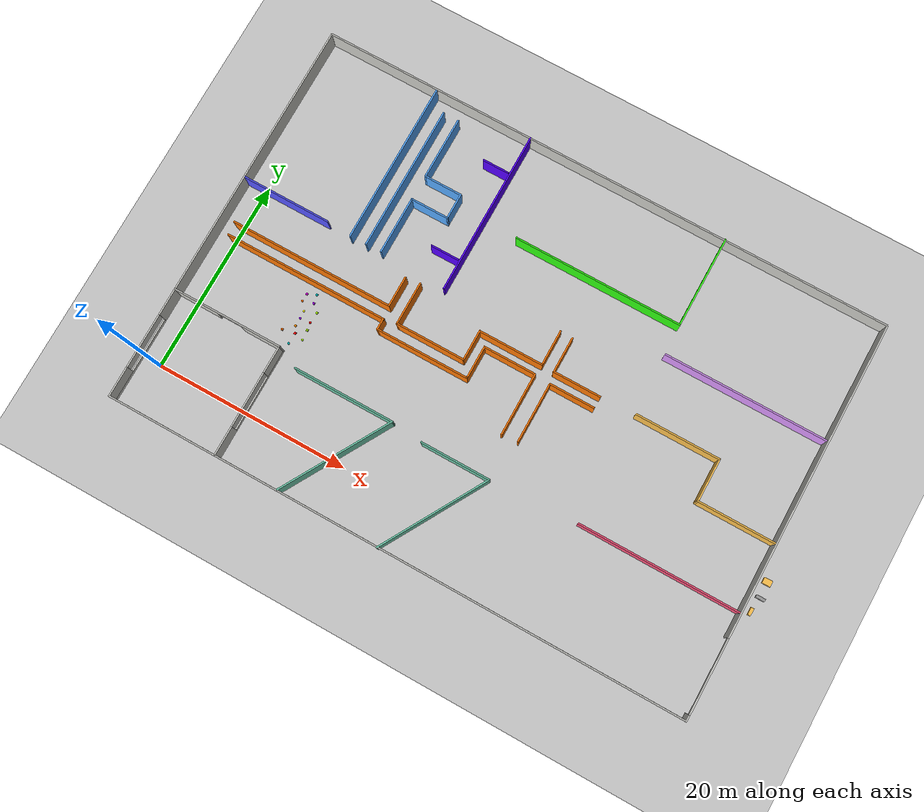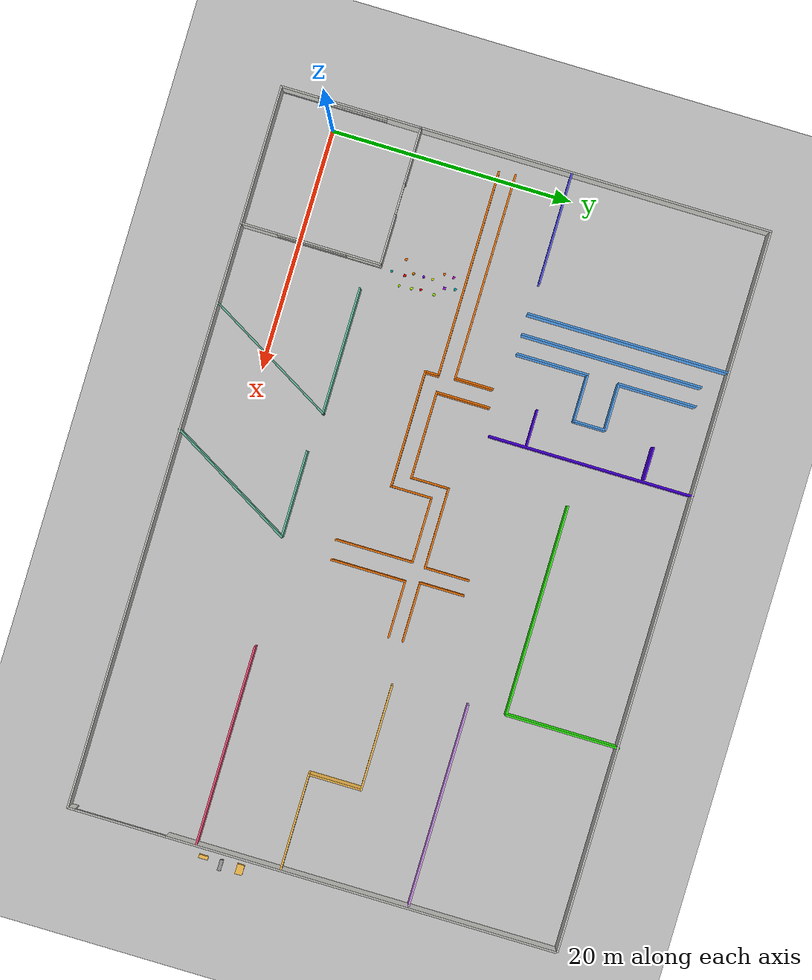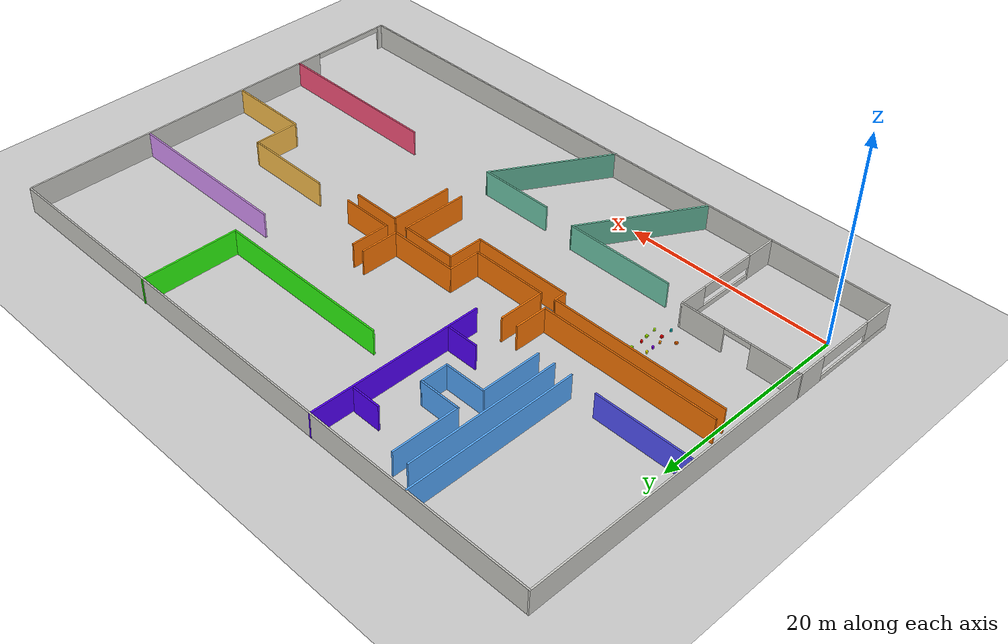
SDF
<sdf version="1.7">
 <world name="default">
  <light name="sun" type="directional">
   <pose>0 0 10 0 -0 0</pose>
   <diffuse>0.8 0.8 0.8 1</diffuse>
   <specular>0.2 0.2 0.2 1</specular>
   <attenuation>
    <range>1000</range>
    <constant>0.9</constant>
    <linear>0.01</linear>
    <quadratic>0.001</quadratic>
   </attenuation>
   <direction>-0.5 0.1 -0.9</direction>
   <spot><inner_angle>0</inner_angle><outer_angle>0</outer_angle><falloff>0</falloff></spot>
  </light>
  <model name="ground_plane">
   <static>1</static>
   <link name="link">
    <collision name="collision">
     <geometry><plane><normal>0 0 1</normal><size>100 100</size></plane></geometry>
     <surface><friction><ode><mu>100</mu><mu2>50</mu2></ode></friction></surface>
    </collision>
    <visual name="visual">
     <cast_shadows>0</cast_shadows>
     <geometry><plane><normal>0 0 1</normal><size>100 100</size></plane></geometry>
     <material>
      <script><uri>file://media/materials/scripts/gazebo.material</uri><name>Gazebo/Grey</name></script>
     </material>
    </visual>
   </link>
  </model>
  <gravity>0 0 -9.8</gravity>
  <magnetic_field>6e-06 2.3e-05 -4.2e-05</magnetic_field>
  <atmosphere type="adiabatic"/>
  <physics type="ode">
   <max_step_size>0.001</max_step_size>
   <real_time_factor>1</real_time_factor>
   <real_time_update_rate>1000</real_time_update_rate>
  </physics>
  <scene><ambient>0.4 0.4 0.4 1</ambient><background>0.7 0.7 0.7 1</background><shadows>1</shadows></scene>
  <spherical_coordinates>
   <surface_model>EARTH_WGS84</surface_model>
   <latitude_deg>0</latitude_deg>
   <longitude_deg>0</longitude_deg>
   <elevation>0</elevation>
   <heading_deg>0</heading_deg>
  </spherical_coordinates>
  <model name="farm_mini">
   <pose>28.0296 15.582 0 0 -0 0</pose>
   <link name="Wall_100">
    <collision name="Wall_100_Collision">
     <geometry><box><size>9.69928 0.15 2.5</size></box></geometry>
     <pose>0 0 1.25 0 -0 0</pose>
    </collision>
    <visual name="Wall_100_Visual">
     <pose>0 0 1.25 0 -0 0</pose>
     <geometry><box><size>9.69928 0.15 2.5</size></box></geometry>
     <material>
      <script><uri>file://media/materials/scripts/gazebo.material</uri><name>Gazebo/Grey</name></script>
      <ambient>0.996078 0.47451 0.0196078 1</ambient>
     </material>
     <meta><layer>0</layer></meta>
    </visual>
    <pose>-6.70176 -2.90377 0 0 -0 0</pose>
   </link>
   <link name="Wall_103">
    <collision name="Wall_103_Collision">
     <geometry><box><size>7.25 0.15 2.5</size></box></geometry>
     <pose>0 0 1.25 0 -0 0</pose>
    </collision>
    <visual name="Wall_103_Visual">
     <pose>0 0 1.25 0 -0 0</pose>
     <geometry><box><size>7.25 0.15 2.5</size></box></geometry>
     <material>
      <script><uri>file://media/materials/scripts/gazebo.material</uri><name>Gazebo/Grey</name></script>
      <ambient>0.996078 0.47451 0.0196078 1</ambient>
     </material>
     <meta><layer>0</layer></meta>
    </visual>
    <pose>-6.59221 -1.55468 0 0 -0 0</pose>
   </link>
   <link name="Wall_104">
    <collision name="Wall_104_Collision">
     <geometry><box><size>3.25 0.15 2.5</size></box></geometry>
     <pose>0 0 1.25 0 -0 0</pose>
    </collision>
    <visual name="Wall_104_Visual">
     <pose>0 0 1.25 0 -0 0</pose>
     <geometry><box><size>3.25 0.15 2.5</size></box></geometry>
     <material>
      <script><uri>file://media/materials/scripts/gazebo.material</uri><name>Gazebo/Grey</name></script>
      <ambient>0.996078 0.47451 0.0196078 1</ambient>
     </material>
     <meta><layer>0</layer></meta>
    </visual>
    <pose>-3.04221 -0.00468 0 0 -0 1.5708</pose>
   </link>
   <link name="Wall_108">
    <collision name="Wall_108_Collision">
     <geometry><box><size>3.5 0.15 2.5</size></box></geometry>
     <pose>0 0 1.25 0 -0 0</pose>
    </collision>
    <visual name="Wall_108_Visual">
     <pose>0 0 1.25 0 -0 0</pose>
     <geometry><box><size>3.5 0.15 2.5</size></box></geometry>
     <material>
      <script><uri>file://media/materials/scripts/gazebo.material</uri><name>Gazebo/Grey</name></script>
      <ambient>0.996078 0.47451 0.0196078 1</ambient>
     </material>
     <meta><layer>0</layer></meta>
    </visual>
    <pose>-1.92712 -1.22877 0 0 -0 1.5708</pose>
   </link>
   <link name="Wall_109">
    <collision name="Wall_109_Collision">
     <geometry><box><size>5.5 0.15 2.5</size></box></geometry>
     <pose>0 0 1.25 0 -0 0</pose>
    </collision>
    <visual name="Wall_109_Visual">
     <pose>0 0 1.25 0 -0 0</pose>
     <geometry><box><size>5.5 0.15 2.5</size></box></geometry>
     <material>
      <script><uri>file://media/materials/scripts/gazebo.material</uri><name>Gazebo/Grey</name></script>
      <ambient>0.996078 0.47451 0.0196078 1</ambient>
     </material>
     <meta><layer>0</layer></meta>
    </visual>
    <pose>0.747884 0.446225 0 0 -0 0</pose>
   </link>
   <link name="Wall_110">
    <collision name="Wall_110_Collision">
     <geometry><box><size>6.5 0.15 2.5</size></box></geometry>
     <pose>0 0 1.25 0 -0 0</pose>
    </collision>
    <visual name="Wall_110_Visual">
     <pose>0 0 1.25 0 -0 0</pose>
     <geometry><box><size>6.5 0.15 2.5</size></box></geometry>
     <material>
      <script><uri>file://media/materials/scripts/gazebo.material</uri><name>Gazebo/Grey</name></script>
      <ambient>0.996078 0.47451 0.0196078 1</ambient>
     </material>
     <meta><layer>0</layer></meta>
    </visual>
    <pose>3.42288 -2.72877 0 0 -0 -1.5708</pose>
   </link>
   <link name="Wall_116">
    <collision name="Wall_116_Collision">
     <geometry><box><size>6.75 0.15 2.5</size></box></geometry>
     <pose>0 0 1.25 0 -0 0</pose>
    </collision>
    <visual name="Wall_116_Visual">
     <pose>0 0 1.25 0 -0 0</pose>
     <geometry><box><size>6.75 0.15 2.5</size></box></geometry>
     <material>
      <script><uri>file://media/materials/scripts/gazebo.material</uri><name>Gazebo/Grey</name></script>
      <ambient>0.996078 0.47451 0.0196078 1</ambient>
     </material>
     <meta><layer>0</layer></meta>
    </visual>
    <pose>0.257793 1.54532 0 0 -0 0</pose>
   </link>
   <link name="Wall_117">
    <collision name="Wall_117_Collision">
     <geometry><box><size>3.75 0.15 2.5</size></box></geometry>
     <pose>0 0 1.25 0 -0 0</pose>
    </collision>
    <visual name="Wall_117_Visual">
     <pose>0 0 1.25 0 -0 0</pose>
     <geometry><box><size>3.75 0.15 2.5</size></box></geometry>
     <material>
      <script><uri>file://media/materials/scripts/gazebo.material</uri><name>Gazebo/Grey</name></script>
      <ambient>0.996078 0.47451 0.0196078 1</ambient>
     </material>
     <meta><layer>0</layer></meta>
    </visual>
    <pose>3.55779 3.34532 0 0 -0 1.5708</pose>
   </link>
   <link name="Wall_119">
    <collision name="Wall_119_Collision">
     <geometry><box><size>3.75 0.15 2.5</size></box></geometry>
     <pose>0 0 1.25 0 -0 0</pose>
    </collision>
    <visual name="Wall_119_Visual">
     <pose>0 0 1.25 0 -0 0</pose>
     <geometry><box><size>3.75 0.15 2.5</size></box></geometry>
     <material>
      <script><uri>file://media/materials/scripts/gazebo.material</uri><name>Gazebo/Grey</name></script>
      <ambient>0.996078 0.47451 0.0196078 1</ambient>
     </material>
     <meta><layer>0</layer></meta>
    </visual>
    <pose>4.82979 3.30181 0 0 -0 -1.5708</pose>
   </link>
   <link name="Wall_120">
    <collision name="Wall_120_Collision">
     <geometry><box><size>5 0.15 2.5</size></box></geometry>
     <pose>0 0 1.25 0 -0 0</pose>
    </collision>
    <visual name="Wall_120_Visual">
     <pose>0 0 1.25 0 -0 0</pose>
     <geometry><box><size>5 0.15 2.5</size></box></geometry>
     <material>
      <script><uri>file://media/materials/scripts/gazebo.material</uri><name>Gazebo/Grey</name></script>
      <ambient>0.996078 0.47451 0.0196078 1</ambient>
     </material>
     <meta><layer>0</layer></meta>
    </visual>
    <pose>7.25479 1.50181 0 0 -0 0</pose>
   </link>
   <link name="Wall_122">
    <collision name="Wall_122_Collision">
     <geometry><box><size>6.25 0.15 2.5</size></box></geometry>
     <pose>0 0 1.25 0 -0 0</pose>
    </collision>
    <visual name="Wall_122_Visual">
     <pose>0 0 1.25 0 -0 0</pose>
     <geometry><box><size>6.25 0.15 2.5</size></box></geometry>
     <material>
      <script><uri>file://media/materials/scripts/gazebo.material</uri><name>Gazebo/Grey</name></script>
      <ambient>0.996078 0.47451 0.0196078 1</ambient>
     </material>
     <meta><layer>0</layer></meta>
    </visual>
    <pose>5.06119 -2.73056 0 0 -0 -1.5708</pose>
   </link>
   <link name="Wall_124">
    <collision name="Wall_124_Collision">
     <geometry><box><size>4.75 0.15 2.5</size></box></geometry>
     <pose>0 0 1.25 0 -0 0</pose>
    </collision>
    <visual name="Wall_124_Visual">
     <pose>0 0 1.25 0 -0 0</pose>
     <geometry><box><size>4.75 0.15 2.5</size></box></geometry>
     <material>
      <script><uri>file://media/materials/scripts/gazebo.material</uri><name>Gazebo/Grey</name></script>
      <ambient>0.996078 0.47451 0.0196078 1</ambient>
     </material>
     <meta><layer>0</layer></meta>
    </visual>
    <pose>7.36119 0.319443 0 0 -0 0</pose>
   </link>
   <link name="Wall_126">
    <collision name="Wall_126_Collision">
     <geometry><box><size>1.25 0.15 2.5</size></box></geometry>
     <pose>0 0 1.25 0 -0 0</pose>
    </collision>
    <visual name="Wall_126_Visual">
     <pose>0 0 1.25 0 -0 0</pose>
     <geometry><box><size>1.25 0.15 2.5</size></box></geometry>
     <material>
      <script><uri>file://media/materials/scripts/gazebo.material</uri><name>Gazebo/Grey</name></script>
      <ambient>0.996078 0.47451 0.0196078 1</ambient>
     </material>
     <meta><layer>0</layer></meta>
    </visual>
    <pose>-11.4764 -2.35377 0 0 -0 -1.5708</pose>
   </link>
   <link name="Wall_129">
    <collision name="Wall_129_Collision">
     <geometry><box><size>4.5 0.15 2.5</size></box></geometry>
     <pose>0 0 1.25 0 -0 0</pose>
    </collision>
    <visual name="Wall_129_Visual">
     <pose>0 0 1.25 0 -0 0</pose>
     <geometry><box><size>4.5 0.15 2.5</size></box></geometry>
     <material>
      <script><uri>file://media/materials/scripts/gazebo.material</uri><name>Gazebo/Grey</name></script>
      <ambient>0.996078 0.47451 0.0196078 1</ambient>
     </material>
     <meta><layer>0</layer></meta>
    </visual>
    <pose>-10.1422 0.62032 0 0 -0 1.5708</pose>
   </link>
   <link name="Wall_131">
    <collision name="Wall_131_Collision">
     <geometry><box><size>3.25 0.15 2.5</size></box></geometry>
     <pose>0 0 1.25 0 -0 0</pose>
    </collision>
    <visual name="Wall_131_Visual">
     <pose>0 0 1.25 0 -0 0</pose>
     <geometry><box><size>3.25 0.15 2.5</size></box></geometry>
     <material>
      <script><uri>file://media/materials/scripts/gazebo.material</uri><name>Gazebo/Grey</name></script>
      <ambient>0.996078 0.47451 0.0196078 1</ambient>
     </material>
     <meta><layer>0</layer></meta>
    </visual>
    <pose>-11.6422 1.09532 0 0 -0 1.5708</pose>
   </link>
   <link name="Wall_26">
    <collision name="Wall_26_Collision">
     <geometry><box><size>11.5 0.15 2.5</size></box></geometry>
     <pose>0 0 1.25 0 -0 0</pose>
    </collision>
    <visual name="Wall_26_Visual">
     <pose>0 0 1.25 0 -0 0</pose>
     <geometry><box><size>11.5 0.15 2.5</size></box></geometry>
     <material>
      <script><uri>file://media/materials/scripts/gazebo.material</uri><name>Gazebo/CeilingTiled</name></script>
      <ambient>0 0.333333 1 1</ambient>
     </material>
     <meta><layer>0</layer></meta>
    </visual>
    <pose>-24.3 -20.3518 0 0 -0 0</pose>
   </link>
   <link name="Wall_27">
    <pose>-18.625 -14.5518 0 0 -0 1.5708</pose>
    <visual name="Wall_27_Visual_0">
     <pose>-4.32558 0 1.25 0 -0 0</pose>
     <geometry><box><size>3.09884 0.15 2.5</size></box></geometry>
     <material>
      <script><uri>file://media/materials/scripts/gazebo.material</uri><name>Gazebo/CeilingTiled</name></script>
      <ambient>0 0.333333 1 1</ambient>
     </material>
     <meta><layer>0</layer></meta>
    </visual>
    <collision name="Wall_27_Collision_0">
     <geometry><box><size>3.09884 0.15 2.5</size></box></geometry>
     <pose>-4.32558 0 1.25 0 -0 0</pose>
    </collision>
    <visual name="Wall_27_Visual_1">
     <pose>1.54942 0 0.25 0 -0 0</pose>
     <geometry><box><size>8.65116 0.15 0.5</size></box></geometry>
     <material>
      <script><uri>file://media/materials/scripts/gazebo.material</uri><name>Gazebo/CeilingTiled</name></script>
      <ambient>0 0.333333 1 1</ambient>
     </material>
     <meta><layer>0</layer></meta>
    </visual>
    <collision name="Wall_27_Collision_1">
     <geometry><box><size>8.65116 0.15 0.5</size></box></geometry>
     <pose>1.54942 0 0.25 0 -0 0</pose>
    </collision>
    <visual name="Wall_27_Visual_2">
     <pose>4.41939 0 1.5 0 -0 0</pose>
     <geometry><box><size>2.91121 0.15 2</size></box></geometry>
     <material>
      <script><uri>file://media/materials/scripts/gazebo.material</uri><name>Gazebo/CeilingTiled</name></script>
      <ambient>0 0.333333 1 1</ambient>
     </material>
     <meta><layer>0</layer></meta>
    </visual>
    <collision name="Wall_27_Collision_2">
     <geometry><box><size>2.91121 0.15 2</size></box></geometry>
     <pose>4.41939 0 1.5 0 -0 0</pose>
    </collision>
    <visual name="Wall_27_Visual_3">
     <pose>0.093817 0 1.9 0 -0 0</pose>
     <geometry><box><size>5.73995 0.15 1.2</size></box></geometry>
     <material>
      <script><uri>file://media/materials/scripts/gazebo.material</uri><name>Gazebo/CeilingTiled</name></script>
      <ambient>0 0.333333 1 1</ambient>
     </material>
     <meta><layer>0</layer></meta>
    </visual>
    <collision name="Wall_27_Collision_3">
     <geometry><box><size>5.73995 0.15 1.2</size></box></geometry>
     <pose>0.093817 0 1.9 0 -0 0</pose>
    </collision>
   </link>
   <link name="Wall_28">
    <pose>-24.3 -8.75179 0 0 -0 3.14159</pose>
    <visual name="Wall_28_Visual_0">
     <pose>-3.6232 0 1.25 0 -0 0</pose>
     <geometry><box><size>4.25359 0.15 2.5</size></box></geometry>
     <material>
      <script><uri>file://media/materials/scripts/gazebo.material</uri><name>Gazebo/CeilingTiled</name></script>
      <ambient>0 0.333333 1 1</ambient>
     </material>
     <meta><layer>0</layer></meta>
    </visual>
    <collision name="Wall_28_Collision_0">
     <geometry><box><size>4.25359 0.15 2.5</size></box></geometry>
     <pose>-3.6232 0 1.25 0 -0 0</pose>
    </collision>
    <visual name="Wall_28_Visual_1">
     <pose>3.40012 0 1.25 0 -0 0</pose>
     <geometry><box><size>4.69976 0.15 2.5</size></box></geometry>
     <material>
      <script><uri>file://media/materials/scripts/gazebo.material</uri><name>Gazebo/CeilingTiled</name></script>
      <ambient>0 0.333333 1 1</ambient>
     </material>
     <meta><layer>0</layer></meta>
    </visual>
    <collision name="Wall_28_Collision_1">
     <geometry><box><size>4.69976 0.15 2.5</size></box></geometry>
     <pose>3.40012 0 1.25 0 -0 0</pose>
    </collision>
    <visual name="Wall_28_Visual_2">
     <pose>-0.223083 0 2.25 0 -0 0</pose>
     <geometry><box><size>2.54665 0.15 0.5</size></box></geometry>
     <material>
      <script><uri>file://media/materials/scripts/gazebo.material</uri><name>Gazebo/CeilingTiled</name></script>
      <ambient>0 0.333333 1 1</ambient>
     </material>
     <meta><layer>0</layer></meta>
    </visual>
    <collision name="Wall_28_Collision_2">
     <geometry><box><size>2.54665 0.15 0.5</size></box></geometry>
     <pose>-0.223083 0 2.25 0 -0 0</pose>
    </collision>
   </link>
   <link name="Wall_29">
    <pose>-29.975 -14.5518 0 0 -0 -1.5708</pose>
    <visual name="Wall_29_Visual_0">
     <pose>-4.41939 0 1.25 0 -0 0</pose>
     <geometry><box><size>2.91121 0.15 2.5</size></box></geometry>
     <material>
      <script><uri>file://media/materials/scripts/gazebo.material</uri><name>Gazebo/CeilingTiled</name></script>
      <ambient>0 0.333333 1 1</ambient>
     </material>
     <meta><layer>0</layer></meta>
    </visual>
    <collision name="Wall_29_Collision_0">
     <geometry><box><size>2.91121 0.15 2.5</size></box></geometry>
     <pose>-4.41939 0 1.25 0 -0 0</pose>
    </collision>
    <visual name="Wall_29_Visual_1">
     <pose>1.45561 0 0.25 0 -0 0</pose>
     <geometry><box><size>8.83879 0.15 0.5</size></box></geometry>
     <material>
      <script><uri>file://media/materials/scripts/gazebo.material</uri><name>Gazebo/CeilingTiled</name></script>
      <ambient>0 0.333333 1 1</ambient>
     </material>
     <meta><layer>0</layer></meta>
    </visual>
    <collision name="Wall_29_Collision_1">
     <geometry><box><size>8.83879 0.15 0.5</size></box></geometry>
     <pose>1.45561 0 0.25 0 -0 0</pose>
    </collision>
    <visual name="Wall_29_Visual_2">
     <pose>4.29127 0 1.5 0 -0 0</pose>
     <geometry><box><size>3.16745 0.15 2</size></box></geometry>
     <material>
      <script><uri>file://media/materials/scripts/gazebo.material</uri><name>Gazebo/CeilingTiled</name></script>
      <ambient>0 0.333333 1 1</ambient>
     </material>
     <meta><layer>0</layer></meta>
    </visual>
    <collision name="Wall_29_Collision_2">
     <geometry><box><size>3.16745 0.15 2</size></box></geometry>
     <pose>4.29127 0 1.5 0 -0 0</pose>
    </collision>
    <visual name="Wall_29_Visual_3">
     <pose>-0.128122 0 1.9 0 -0 0</pose>
     <geometry><box><size>5.67134 0.15 1.2</size></box></geometry>
     <material>
      <script><uri>file://media/materials/scripts/gazebo.material</uri><name>Gazebo/CeilingTiled</name></script>
      <ambient>0 0.333333 1 1</ambient>
     </material>
     <meta><layer>0</layer></meta>
    </visual>
    <collision name="Wall_29_Collision_3">
     <geometry><box><size>5.67134 0.15 1.2</size></box></geometry>
     <pose>-0.128122 0 1.9 0 -0 0</pose>
    </collision>
   </link>
   <link name="Wall_43">
    <collision name="Wall_43_Collision">
     <geometry><box><size>29.25 0.15 2.5</size></box></geometry>
     <pose>0 0 1.25 0 -0 0</pose>
    </collision>
    <visual name="Wall_43_Visual">
     <pose>0 0 1.25 0 -0 0</pose>
     <geometry><box><size>29.25 0.15 2.5</size></box></geometry>
     <material>
      <script><uri>file://media/materials/scripts/gazebo.material</uri><name>Gazebo/CeilingTiled</name></script>
      <ambient>1 0.666667 0.498039 1</ambient>
     </material>
     <meta><layer>0</layer></meta>
    </visual>
    <pose>-29.975 5.79821 0 0 -0 1.5708</pose>
   </link>
   <link name="Wall_44">
    <collision name="Wall_44_Collision">
     <geometry><box><size>60 0.15 2.5</size></box></geometry>
     <pose>0 0 1.25 0 -0 0</pose>
    </collision>
    <visual name="Wall_44_Visual">
     <pose>0 0 1.25 0 -0 0</pose>
     <geometry><box><size>60 0.15 2.5</size></box></geometry>
     <material>
      <script><uri>file://media/materials/scripts/gazebo.material</uri><name>Gazebo/CeilingTiled</name></script>
      <ambient>1 0.666667 0.498039 1</ambient>
     </material>
     <meta><layer>0</layer></meta>
    </visual>
    <pose>-0.049998 20.3482 0 0 -0 0</pose>
   </link>
   <link name="Wall_47">
    <collision name="Wall_47_Collision">
     <geometry><box><size>48.75 0.15 2.5</size></box></geometry>
     <pose>0 0 1.25 0 -0 0</pose>
    </collision>
    <visual name="Wall_47_Visual">
     <pose>0 0 1.25 0 -0 0</pose>
     <geometry><box><size>48.75 0.15 2.5</size></box></geometry>
     <material>
      <script><uri>file://media/materials/scripts/gazebo.material</uri><name>Gazebo/CeilingTiled</name></script>
      <ambient>1 0.666667 0.498039 1</ambient>
     </material>
     <meta><layer>0</layer></meta>
    </visual>
    <pose>5.675 -20.3518 0 0 -0 0</pose>
   </link>
   <link name="Wall_49">
    <pose>29.975 -0.05179 0 0 -0 1.5708</pose>
    <visual name="Wall_49_Visual_0">
     <pose>-20.0365 0 1.25 0 -0 0</pose>
     <geometry><box><size>0.676976 0.15 2.5</size></box></geometry>
     <material>
      <script><uri>file://media/materials/scripts/gazebo.material</uri><name>Gazebo/CeilingTiled</name></script>
      <ambient>0.996078 0.47451 0.0196078 1</ambient>
     </material>
     <meta><layer>0</layer></meta>
    </visual>
    <collision name="Wall_49_Collision_0">
     <geometry><box><size>0.676976 0.15 2.5</size></box></geometry>
     <pose>-20.0365 0 1.25 0 -0 0</pose>
    </collision>
    <visual name="Wall_49_Visual_1">
     <pose>4.12412 0 1.25 0 -0 0</pose>
     <geometry><box><size>32.5018 0.15 2.5</size></box></geometry>
     <material>
      <script><uri>file://media/materials/scripts/gazebo.material</uri><name>Gazebo/CeilingTiled</name></script>
      <ambient>0.996078 0.47451 0.0196078 1</ambient>
     </material>
     <meta><layer>0</layer></meta>
    </visual>
    <collision name="Wall_49_Collision_1">
     <geometry><box><size>32.5018 0.15 2.5</size></box></geometry>
     <pose>4.12412 0 1.25 0 -0 0</pose>
    </collision>
    <visual name="Wall_49_Visual_2">
     <pose>-15.9124 0 2.25 0 -0 0</pose>
     <geometry><box><size>7.57127 0.15 0.5</size></box></geometry>
     <material>
      <script><uri>file://media/materials/scripts/gazebo.material</uri><name>Gazebo/CeilingTiled</name></script>
      <ambient>0.996078 0.47451 0.0196078 1</ambient>
     </material>
     <meta><layer>0</layer></meta>
    </visual>
    <collision name="Wall_49_Collision_2">
     <geometry><box><size>7.57127 0.15 0.5</size></box></geometry>
     <pose>-15.9124 0 2.25 0 -0 0</pose>
    </collision>
   </link>
   <link name="Wall_53">
    <collision name="Wall_53_Collision">
     <geometry><box><size>16.75 0.15 2.5</size></box></geometry>
     <pose>0 0 1.25 0 -0 0</pose>
    </collision>
    <visual name="Wall_53_Visual">
     <pose>0 0 1.25 0 -0 0</pose>
     <geometry><box><size>16.75 0.15 2.5</size></box></geometry>
     <material>
      <script><uri>file://media/materials/scripts/gazebo.material</uri><name>Gazebo/Grey</name></script>
      <ambient>0.866667 0.596078 1 1</ambient>
     </material>
     <meta><layer>0</layer></meta>
    </visual>
    <pose>21.443 7.9453 0 0 -0 0</pose>
   </link>
   <link name="Wall_55">
    <collision name="Wall_55_Collision">
     <geometry><box><size>9.5 0.15 2.5</size></box></geometry>
     <pose>0 0 1.25 0 -0 0</pose>
    </collision>
    <visual name="Wall_55_Visual">
     <pose>0 0 1.25 0 -0 0</pose>
     <geometry><box><size>9.5 0.15 2.5</size></box></geometry>
     <material>
      <script><uri>file://media/materials/scripts/gazebo.material</uri><name>Gazebo/Grey</name></script>
      <ambient>0.188235 1 0.0666667 1</ambient>
     </material>
     <meta><layer>0</layer></meta>
    </visual>
    <pose>12.987 15.7525 0 0 -0 -1.5708</pose>
   </link>
   <link name="Wall_57">
    <collision name="Wall_57_Collision">
     <geometry><box><size>8 0.15 2.5</size></box></geometry>
     <pose>0 0 1.25 0 -0 0</pose>
    </collision>
    <visual name="Wall_57_Visual">
     <pose>0 0 1.25 0 -0 0</pose>
     <geometry><box><size>8 0.15 2.5</size></box></geometry>
     <material>
      <script><uri>file://media/materials/scripts/gazebo.material</uri><name>Gazebo/Grey</name></script>
      <ambient>1 0.764706 0.305882 1</ambient>
     </material>
     <meta><layer>0</layer></meta>
    </visual>
    <pose>25.9129 -2.66452 0 0 -0 3.14159</pose>
   </link>
   <link name="Wall_58">
    <collision name="Wall_58_Collision">
     <geometry><box><size>4.5 0.15 2.5</size></box></geometry>
     <pose>0 0 1.25 0 -0 0</pose>
    </collision>
    <visual name="Wall_58_Visual">
     <pose>0 0 1.25 0 -0 0</pose>
     <geometry><box><size>4.5 0.15 2.5</size></box></geometry>
     <material>
      <script><uri>file://media/materials/scripts/gazebo.material</uri><name>Gazebo/Grey</name></script>
      <ambient>1 0.764706 0.305882 1</ambient>
     </material>
     <meta><layer>0</layer></meta>
    </visual>
    <pose>21.9879 -0.489521 0 0 -0 1.5708</pose>
   </link>
   <link name="Wall_59">
    <collision name="Wall_59_Collision">
     <geometry><box><size>8.75 0.15 2.5</size></box></geometry>
     <pose>0 0 1.25 0 -0 0</pose>
    </collision>
    <visual name="Wall_59_Visual">
     <pose>0 0 1.25 0 -0 0</pose>
     <geometry><box><size>8.75 0.15 2.5</size></box></geometry>
     <material>
      <script><uri>file://media/materials/scripts/gazebo.material</uri><name>Gazebo/Grey</name></script>
      <ambient>1 0.764706 0.305882 1</ambient>
     </material>
     <meta><layer>0</layer></meta>
    </visual>
    <pose>17.6879 1.68548 0 0 -0 3.14159</pose>
   </link>
   <link name="Wall_61">
    <collision name="Wall_61_Collision">
     <geometry><box><size>16.5 0.15 2.5</size></box></geometry>
     <pose>0 0 1.25 0 -0 0</pose>
    </collision>
    <visual name="Wall_61_Visual">
     <pose>0 0 1.25 0 -0 0</pose>
     <geometry><box><size>16.5 0.15 2.5</size></box></geometry>
     <material>
      <script><uri>file://media/materials/scripts/gazebo.material</uri><name>Gazebo/Grey</name></script>
      <ambient>1 0.333333 0.498039 1</ambient>
     </material>
     <meta><layer>0</layer></meta>
    </visual>
    <pose>21.6629 -9.68573 0 0 -0 3.14159</pose>
   </link>
   <link name="Wall_64">
    <collision name="Wall_64_Collision">
     <geometry><box><size>16.75 0.15 2.5</size></box></geometry>
     <pose>0 0 1.25 0 -0 0</pose>
    </collision>
    <visual name="Wall_64_Visual">
     <pose>0 0 1.25 0 -0 0</pose>
     <geometry><box><size>16.75 0.15 2.5</size></box></geometry>
     <material>
      <script><uri>file://media/materials/scripts/gazebo.material</uri><name>Gazebo/Grey</name></script>
      <ambient>0.333333 0.666667 1 1</ambient>
     </material>
     <meta><layer>0</layer></meta>
    </visual>
    <pose>-18.2184 11.9714 0 0 -0 -1.5708</pose>
   </link>
   <link name="Wall_67">
    <collision name="Wall_67_Collision">
     <geometry><box><size>15 0.15 2.5</size></box></geometry>
     <pose>0 0 1.25 0 -0 0</pose>
    </collision>
    <visual name="Wall_67_Visual">
     <pose>0 0 1.25 0 -0 0</pose>
     <geometry><box><size>15 0.15 2.5</size></box></geometry>
     <material>
      <script><uri>file://media/materials/scripts/gazebo.material</uri><name>Gazebo/Grey</name></script>
      <ambient>0.333333 0.666667 1 1</ambient>
     </material>
     <meta><layer>0</layer></meta>
    </visual>
    <pose>-16.5021 11.1274 0 0 -0 1.5708</pose>
   </link>
   <link name="Wall_69">
    <collision name="Wall_69_Collision">
     <geometry><box><size>6.5 0.15 2.5</size></box></geometry>
     <pose>0 0 1.25 0 -0 0</pose>
    </collision>
    <visual name="Wall_69_Visual">
     <pose>0 0 1.25 0 -0 0</pose>
     <geometry><box><size>6.5 0.15 2.5</size></box></geometry>
     <material>
      <script><uri>file://media/materials/scripts/gazebo.material</uri><name>Gazebo/Grey</name></script>
      <ambient>0.333333 0.666667 1 1</ambient>
     </material>
     <meta><layer>0</layer></meta>
    </visual>
    <pose>-14.9021 15.3774 0 0 -0 -1.5708</pose>
   </link>
   <link name="Wall_70">
    <collision name="Wall_70_Collision">
     <geometry><box><size>4 0.15 2.5</size></box></geometry>
     <pose>0 0 1.25 0 -0 0</pose>
    </collision>
    <visual name="Wall_70_Visual">
     <pose>0 0 1.25 0 -0 0</pose>
     <geometry><box><size>4 0.15 2.5</size></box></geometry>
     <material>
      <script><uri>file://media/materials/scripts/gazebo.material</uri><name>Gazebo/Grey</name></script>
      <ambient>0.333333 0.666667 1 1</ambient>
     </material>
     <meta><layer>0</layer></meta>
    </visual>
    <pose>-12.9771 12.2024 0 0 -0 0</pose>
   </link>
   <link name="Wall_71">
    <collision name="Wall_71_Collision">
     <geometry><box><size>2.75 0.15 2.5</size></box></geometry>
     <pose>0 0 1.25 0 -0 0</pose>
    </collision>
    <visual name="Wall_71_Visual">
     <pose>0 0 1.25 0 -0 0</pose>
     <geometry><box><size>2.75 0.15 2.5</size></box></geometry>
     <material>
      <script><uri>file://media/materials/scripts/gazebo.material</uri><name>Gazebo/Grey</name></script>
      <ambient>0.333333 0.666667 1 1</ambient>
     </material>
     <meta><layer>0</layer></meta>
    </visual>
    <pose>-11.0521 10.9024 0 0 -0 -1.5708</pose>
   </link>
   <link name="Wall_72">
    <collision name="Wall_72_Collision">
     <geometry><box><size>4 0.15 2.5</size></box></geometry>
     <pose>0 0 1.25 0 -0 0</pose>
    </collision>
    <visual name="Wall_72_Visual">
     <pose>0 0 1.25 0 -0 0</pose>
     <geometry><box><size>4 0.15 2.5</size></box></geometry>
     <material>
      <script><uri>file://media/materials/scripts/gazebo.material</uri><name>Gazebo/Grey</name></script>
      <ambient>0.333333 0.666667 1 1</ambient>
     </material>
     <meta><layer>0</layer></meta>
    </visual>
    <pose>-12.9771 9.60244 0 0 -0 3.14159</pose>
   </link>
   <link name="Wall_73">
    <collision name="Wall_73_Collision">
     <geometry><box><size>6 0.15 2.5</size></box></geometry>
     <pose>0 0 1.25 0 -0 0</pose>
    </collision>
    <visual name="Wall_73_Visual">
     <pose>0 0 1.25 0 -0 0</pose>
     <geometry><box><size>6 0.15 2.5</size></box></geometry>
     <material>
      <script><uri>file://media/materials/scripts/gazebo.material</uri><name>Gazebo/Grey</name></script>
      <ambient>0.333333 0.666667 1 1</ambient>
     </material>
     <meta><layer>0</layer></meta>
    </visual>
    <pose>-14.9021 6.67744 0 0 -0 -1.5708</pose>
   </link>
   <link name="Wall_77">
    <collision name="Wall_77_Collision">
     <geometry><box><size>17 0.15 2.5</size></box></geometry>
     <pose>0 0 1.25 0 -0 0</pose>
    </collision>
    <visual name="Wall_77_Visual">
     <pose>0 0 1.25 0 -0 0</pose>
     <geometry><box><size>17 0.15 2.5</size></box></geometry>
     <material>
      <script><uri>file://media/materials/scripts/gazebo.material</uri><name>Gazebo/Grey</name></script>
      <ambient>0.333333 0 1 1</ambient>
     </material>
     <meta><layer>0</layer></meta>
    </visual>
    <pose>-7.96607 11.9326 0 0 -0 -1.5708</pose>
   </link>
   <link name="Wall_79">
    <collision name="Wall_79_Collision">
     <geometry><box><size>3 0.15 2.5</size></box></geometry>
     <pose>0 0 1.25 0 -0 0</pose>
    </collision>
    <visual name="Wall_79_Visual">
     <pose>0 0 1.25 0 -0 0</pose>
     <geometry><box><size>3 0.15 2.5</size></box></geometry>
     <material>
      <script><uri>file://media/materials/scripts/gazebo.material</uri><name>Gazebo/Grey</name></script>
      <ambient>0.333333 0 1 1</ambient>
     </material>
     <meta><layer>0</layer></meta>
    </visual>
    <pose>-9.5705 6.5414 0 0 -0 3.14159</pose>
   </link>
   <link name="Wall_81">
    <collision name="Wall_81_Collision">
     <geometry><box><size>2.75 0.15 2.5</size></box></geometry>
     <pose>0 0 1.25 0 -0 0</pose>
    </collision>
    <visual name="Wall_81_Visual">
     <pose>0 0 1.25 0 -0 0</pose>
     <geometry><box><size>2.75 0.15 2.5</size></box></geometry>
     <material>
      <script><uri>file://media/materials/scripts/gazebo.material</uri><name>Gazebo/Grey</name></script>
      <ambient>0.333333 0 1 1</ambient>
     </material>
     <meta><layer>0</layer></meta>
    </visual>
    <pose>-9.48742 16.29 0 0 -0 3.14159</pose>
   </link>
   <link name="Wall_83">
    <collision name="Wall_83_Collision">
     <geometry><box><size>9.25 0.15 2.5</size></box></geometry>
     <pose>0 0 1.25 0 -0 0</pose>
    </collision>
    <visual name="Wall_83_Visual">
     <pose>0 0 1.25 0 -0 0</pose>
     <geometry><box><size>9.25 0.15 2.5</size></box></geometry>
     <material>
      <script><uri>file://media/materials/scripts/gazebo.material</uri><name>Gazebo/Grey</name></script>
      <ambient>0.333333 0.333333 1 1</ambient>
     </material>
     <meta><layer>0</layer></meta>
    </visual>
    <pose>-25.3842 3.8272 0 0 -0 0</pose>
   </link>
   <link name="Wall_85">
    <collision name="Wall_85_Collision">
     <geometry><box><size>12.25 0.15 2.5</size></box></geometry>
     <pose>0 0 1.25 0 -0 0</pose>
    </collision>
    <visual name="Wall_85_Visual">
     <pose>0 0 1.25 0 -0 0</pose>
     <geometry><box><size>12.25 0.15 2.5</size></box></geometry>
     <material>
      <script><uri>file://media/materials/scripts/gazebo.material</uri><name>Gazebo/Grey</name></script>
      <ambient>0.435294 0.796078 0.67451 1</ambient>
     </material>
     <meta><layer>0</layer></meta>
    </visual>
    <pose>-8.9743 -15.0256 0 0 -0 1.0472</pose>
   </link>
   <link name="Wall_87">
    <collision name="Wall_87_Collision">
     <geometry><box><size>12 0.15 2.5</size></box></geometry>
     <pose>0 0 1.25 0 -0 0</pose>
    </collision>
    <visual name="Wall_87_Visual">
     <pose>0 0 1.25 0 -0 0</pose>
     <geometry><box><size>12 0.15 2.5</size></box></geometry>
     <material>
      <script><uri>file://media/materials/scripts/gazebo.material</uri><name>Gazebo/Grey</name></script>
      <ambient>0.435294 0.796078 0.67451 1</ambient>
     </material>
     <meta><layer>0</layer></meta>
    </visual>
    <pose>1.48614 -15.2688 0 0 -0 1.0472</pose>
   </link>
   <link name="Wall_88">
    <collision name="Wall_88_Collision">
     <geometry><box><size>7.25 0.15 2.5</size></box></geometry>
     <pose>0 0 1.25 0 -0 0</pose>
    </collision>
    <visual name="Wall_88_Visual">
     <pose>0 0 1.25 0 -0 0</pose>
     <geometry><box><size>7.25 0.15 2.5</size></box></geometry>
     <material>
      <script><uri>file://media/materials/scripts/gazebo.material</uri><name>Gazebo/Grey</name></script>
      <ambient>0.435294 0.796078 0.67451 1</ambient>
     </material>
     <meta><layer>0</layer></meta>
    </visual>
    <pose>0.898635 -10.1376 0 0 -0 3.14159</pose>
   </link>
   <link name="Wall_91">
    <collision name="Wall_91_Collision">
     <geometry><box><size>10.5 0.15 2.5</size></box></geometry>
     <pose>0 0 1.25 0 -0 0</pose>
    </collision>
    <visual name="Wall_91_Visual">
     <pose>0 0 1.25 0 -0 0</pose>
     <geometry><box><size>10.5 0.15 2.5</size></box></geometry>
     <material>
      <script><uri>file://media/materials/scripts/gazebo.material</uri><name>Gazebo/Grey</name></script>
      <ambient>0.435294 0.796078 0.67451 1</ambient>
     </material>
     <meta><layer>0</layer></meta>
    </visual>
    <pose>-11.1243 -9.78618 0 0 -0 3.14159</pose>
   </link>
   <link name="Wall_94">
    <collision name="Wall_94_Collision">
     <geometry><box><size>17.5 0.15 2.5</size></box></geometry>
     <pose>0 0 1.25 0 -0 0</pose>
    </collision>
    <visual name="Wall_94_Visual">
     <pose>0 0 1.25 0 -0 0</pose>
     <geometry><box><size>17.5 0.15 2.5</size></box></geometry>
     <material>
      <script><uri>file://media/materials/scripts/gazebo.material</uri><name>Gazebo/Grey</name></script>
      <ambient>0.188235 1 0.0666667 1</ambient>
     </material>
     <meta><layer>0</layer></meta>
    </visual>
    <pose>4.31195 11.0775 0 0 -0 3.14159</pose>
   </link>
   <link name="Wall_96">
    <collision name="Wall_96_Collision">
     <geometry><box><size>17 0.15 2.5</size></box></geometry>
     <pose>0 0 1.25 0 -0 0</pose>
    </collision>
    <visual name="Wall_96_Visual">
     <pose>0 0 1.25 0 -0 0</pose>
     <geometry><box><size>17 0.15 2.5</size></box></geometry>
     <material>
      <script><uri>file://media/materials/scripts/gazebo.material</uri><name>Gazebo/Grey</name></script>
      <ambient>0.996078 0.47451 0.0196078 1</ambient>
     </material>
     <meta><layer>0</layer></meta>
    </visual>
    <pose>-20.0672 -0.45468 0 0 -0 0</pose>
   </link>
   <link name="Wall_98">
    <collision name="Wall_98_Collision">
     <geometry><box><size>17 0.15 2.5</size></box></geometry>
     <pose>0 0 1.25 0 -0 0</pose>
    </collision>
    <visual name="Wall_98_Visual">
     <pose>0 0 1.25 0 -0 0</pose>
     <geometry><box><size>17 0.15 2.5</size></box></geometry>
     <material>
      <script><uri>file://media/materials/scripts/gazebo.material</uri><name>Gazebo/Grey</name></script>
      <ambient>0.996078 0.47451 0.0196078 1</ambient>
     </material>
     <meta><layer>0</layer></meta>
    </visual>
    <pose>-19.9014 -1.80377 0 0 -0 0</pose>
   </link>
   <static>1</static>
  </model>
  <model name="Box_15x30_0_clone_clone">
   <link name="Wall">
    <pose>0 0 0.1985 0 -0 0</pose>
    <inertial>
     <mass>5</mass>
     <inertia><ixx>0.3089</ixx><iyy>0.1022</iyy><izz>0.2797</izz><ixy>0</ixy><ixz>0</ixz><iyz>0</iyz></inertia>
    </inertial>
    <collision name="Wall_Collision"><geometry><box><size>0.296 0.764 0.397</size></box></geometry></collision>
    <visual name="Wall_Visual">
     <geometry><box><size>0.296 0.764 0.397</size></box></geometry>
     <material>
      <script><uri>file://media/materials/scripts/gazebo.material</uri><name>Gazebo/Grey</name></script>
      <ambient>1 0.764706 0.305882 1</ambient>
     </material>
    </visual>
   </link>
   <static>1</static>
   <pose>59.0264 6.6425 0 0 -0 0</pose>
  </model>
  <model name="Box_36x15W_clone_clone">
   <link name="Wall">
    <pose>0 0 0.1985 0 -0 0</pose>
    <inertial>
     <mass>5</mass>
     <inertia><ixx>0.1022</ixx><iyy>0.4107</iyy><izz>0.3815</izz><ixy>0</ixy><ixz>0</ixz><iyz>0</iyz></inertia>
    </inertial>
    <collision name="Wall_Collision"><geometry><box><size>0.91 0.296 0.397</size></box></geometry></collision>
    <visual name="Wall_Visual">
     <geometry><box><size>0.91 0.296 0.397</size></box></geometry>
     <material>
      <script><uri>file://media/materials/scripts/gazebo.material</uri><name>Gazebo/Grey</name></script>
      <ambient>1 1 1 1</ambient>
     </material>
    </visual>
   </link>
   <static>1</static>
   <pose>59.2667 8.13189 0 0 -0 0</pose>
  </model>
  <model name="Box_33x15_clone_clone">
   <link name="Wall">
    <pose>0 0 0.1985 0 -0 0</pose>
    <inertial>
     <mass>5</mass>
     <inertia><ixx>0.2157</ixx><iyy>0.3597</iyy><izz>0.444</izz><ixy>0</ixy><ixz>0</ixz><iyz>0</iyz></inertia>
    </inertial>
    <collision name="Wall_Collision"><geometry><box><size>0.84 0.6 0.397</size></box></geometry></collision>
    <visual name="Wall_Visual">
     <geometry><box><size>0.84 0.6 0.397</size></box></geometry>
     <material>
      <script><uri>file://media/materials/scripts/gazebo.material</uri><name>Gazebo/Grey</name></script>
      <ambient>1 0.764706 0.305882 1</ambient>
     </material>
    </visual>
   </link>
   <static>1</static>
   <pose>59.1588 9.72993 0 0 -0 0</pose>
  </model>
  <model name="cube_or">
   <link name="link_2">
    <pose>0 0 0.1 0 -0 0</pose>
    <inertial>
     <mass>1</mass>
     <inertia>
      <ixx>0.166667</ixx>
      <ixy>0</ixy>
      <ixz>0</ixz>
      <iyy>0.166667</iyy>
      <iyz>0</iyz>
      <izz>0.166667</izz>
     </inertia>
    </inertial>
    <visual name="visual">
     <geometry><box><size>0.2 0.2 0.2</size></box></geometry>
     <material>
      <lighting>1</lighting>
      <script><uri>file://media/materials/scripts/gazebo.material</uri><name>Gazebo/Grey</name></script>
      <ambient>1 0.416 0 1</ambient>
      <diffuse>1 0.416 0 1</diffuse>
      <specular>0 0 0 1</specular>
      <emissive>0 0 0 1</emissive>
      <shader type="vertex"><normal_map>__default__</normal_map></shader>
     </material>
    </visual>
    <collision name="collision">
     <geometry><box><size>0.2 0.2 0.2</size></box></geometry>
     <surface>
      <friction>
       <ode><mu>1</mu><mu2>1</mu2><fdir1>0 0 0</fdir1><slip1>0</slip1><slip2>0</slip2></ode>
       <torsional>
        <coefficient>1</coefficient>
        <patch_radius>0</patch_radius>
        <surface_radius>0</surface_radius>
        <use_patch_radius>1</use_patch_radius>
        <ode><slip>0</slip></ode>
       </torsional>
      </friction>
      <bounce><restitution_coefficient>0</restitution_coefficient><threshold>1e+06</threshold></bounce>
      <contact>
       <collide_without_contact>0</collide_without_contact>
       <collide_without_contact_bitmask>1</collide_without_contact_bitmask>
       <collide_bitmask>1</collide_bitmask>
       <ode>
        <soft_cfm>0</soft_cfm>
        <soft_erp>0.2</soft_erp>
        <kp>1e+13</kp>
        <kd>1</kd>
        <max_vel>0.01</max_vel>
        <min_depth>0</min_depth>
       </ode>
       <bullet>
        <split_impulse>1</split_impulse>
        <split_impulse_penetration_threshold>-0.01</split_impulse_penetration_threshold>
        <soft_cfm>0</soft_cfm>
        <soft_erp>0.2</soft_erp>
        <kp>1e+13</kp>
        <kd>1</kd>
       </bullet>
      </contact>
     </surface>
    </collision>
   </link>
   <static>1</static>
   <pose>8.22157 8.6173 0 0 -0 0</pose>
  </model>
  <model name="cylinder_o">
   <link name="link_0">
    <pose>0 0 0.1 0 -0 0</pose>
    <inertial>
     <mass>1</mass>
     <inertia><ixx>0.145833</ixx><ixy>0</ixy><ixz>0</ixz><iyy>0.145833</iyy><iyz>0</iyz><izz>0.125</izz></inertia>
    </inertial>
    <visual name="visual">
     <geometry><cylinder><radius>0.1</radius><length>0.2</length></cylinder></geometry>
     <material>
      <lighting>1</lighting>
      <script><uri>file://media/materials/scripts/gazebo.material</uri><name>Gazebo/Grey</name></script>
      <ambient>1 0.561 0 1</ambient>
      <diffuse>1 0.561 0 1</diffuse>
      <specular>0 0 0 1</specular>
      <emissive>0 0 0 1</emissive>
      <shader type="vertex"><normal_map>__default__</normal_map></shader>
     </material>
    </visual>
    <collision name="collision">
     <geometry><cylinder><radius>0.1</radius><length>0.2</length></cylinder></geometry>
     <surface>
      <friction>
       <ode><mu>1</mu><mu2>1</mu2><fdir1>0 0 0</fdir1><slip1>0</slip1><slip2>0</slip2></ode>
       <torsional>
        <coefficient>1</coefficient>
        <patch_radius>0</patch_radius>
        <surface_radius>0</surface_radius>
        <use_patch_radius>1</use_patch_radius>
        <ode><slip>0</slip></ode>
       </torsional>
      </friction>
      <bounce><restitution_coefficient>0</restitution_coefficient><threshold>1e+06</threshold></bounce>
      <contact>
       <collide_without_contact>0</collide_without_contact>
       <collide_without_contact_bitmask>1</collide_without_contact_bitmask>
       <collide_bitmask>1</collide_bitmask>
       <ode>
        <soft_cfm>0</soft_cfm>
        <soft_erp>0.2</soft_erp>
        <kp>1e+13</kp>
        <kd>1</kd>
        <max_vel>0.01</max_vel>
        <min_depth>0</min_depth>
       </ode>
       <bullet>
        <split_impulse>1</split_impulse>
        <split_impulse_penetration_threshold>-0.01</split_impulse_penetration_threshold>
        <soft_cfm>0</soft_cfm>
        <soft_erp>0.2</soft_erp>
        <kp>1e+13</kp>
        <kd>1</kd>
       </bullet>
      </contact>
     </surface>
    </collision>
   </link>
   <static>1</static>
   <pose>9.15065 9.50932 0 0 -0 0</pose>
  </model>
  <model name="cube_r">
   <link name="link_2">
    <pose>0 0 0.1 0 -0 0</pose>
    <inertial>
     <mass>1</mass>
     <inertia>
      <ixx>0.166667</ixx>
      <ixy>0</ixy>
      <ixz>0</ixz>
      <iyy>0.166667</iyy>
      <iyz>0</iyz>
      <izz>0.166667</izz>
     </inertia>
    </inertial>
    <visual name="visual">
     <geometry><box><size>0.2 0.2 0.2</size></box></geometry>
     <material>
      <lighting>1</lighting>
      <script><uri>file://media/materials/scripts/gazebo.material</uri><name>Gazebo/Grey</name></script>
      <ambient>1 0 0 1</ambient>
      <diffuse>1 0 0 1</diffuse>
      <specular>0 0 0 1</specular>
      <emissive>0 0 0 1</emissive>
      <shader type="vertex"><normal_map>__default__</normal_map></shader>
     </material>
    </visual>
    <collision name="collision">
     <geometry><box><size>0.2 0.2 0.2</size></box></geometry>
     <surface>
      <friction>
       <ode><mu>1</mu><mu2>1</mu2><fdir1>0 0 0</fdir1><slip1>0</slip1><slip2>0</slip2></ode>
       <torsional>
        <coefficient>1</coefficient>
        <patch_radius>0</patch_radius>
        <surface_radius>0</surface_radius>
        <use_patch_radius>1</use_patch_radius>
        <ode><slip>0</slip></ode>
       </torsional>
      </friction>
      <bounce><restitution_coefficient>0</restitution_coefficient><threshold>1e+06</threshold></bounce>
      <contact>
       <collide_without_contact>0</collide_without_contact>
       <collide_without_contact_bitmask>1</collide_without_contact_bitmask>
       <collide_bitmask>1</collide_bitmask>
       <ode>
        <soft_cfm>0</soft_cfm>
        <soft_erp>0.2</soft_erp>
        <kp>1e+13</kp>
        <kd>1</kd>
        <max_vel>0.01</max_vel>
        <min_depth>0</min_depth>
       </ode>
       <bullet>
        <split_impulse>1</split_impulse>
        <split_impulse_penetration_threshold>-0.01</split_impulse_penetration_threshold>
        <soft_cfm>0</soft_cfm>
        <soft_erp>0.2</soft_erp>
        <kp>1e+13</kp>
        <kd>1</kd>
       </bullet>
      </contact>
     </surface>
    </collision>
   </link>
   <static>1</static>
   <pose>9.49713 8.86777 0 0 -0 0</pose>
  </model>
  <model name="cube_gy">
   <link name="link_2">
    <pose>0 0 0.1 0 -0 0</pose>
    <inertial>
     <mass>1</mass>
     <inertia>
      <ixx>0.166667</ixx>
      <ixy>0</ixy>
      <ixz>0</ixz>
      <iyy>0.166667</iyy>
      <iyz>0</iyz>
      <izz>0.166667</izz>
     </inertia>
    </inertial>
    <visual name="visual">
     <geometry><box><size>0.2 0.2 0.2</size></box></geometry>
     <material>
      <lighting>1</lighting>
      <script><uri>file://media/materials/scripts/gazebo.material</uri><name>Gazebo/Grey</name></script>
      <ambient>0.675 1 0 1</ambient>
      <diffuse>0.675 1 0 1</diffuse>
      <specular>0 0 0 1</specular>
      <emissive>0 0 0 1</emissive>
      <shader type="vertex"><normal_map>__default__</normal_map></shader>
     </material>
    </visual>
    <collision name="collision">
     <geometry><box><size>0.2 0.2 0.2</size></box></geometry>
     <surface>
      <friction>
       <ode><mu>1</mu><mu2>1</mu2><fdir1>0 0 0</fdir1><slip1>0</slip1><slip2>0</slip2></ode>
       <torsional>
        <coefficient>1</coefficient>
        <patch_radius>0</patch_radius>
        <surface_radius>0</surface_radius>
        <use_patch_radius>1</use_patch_radius>
        <ode><slip>0</slip></ode>
       </torsional>
      </friction>
      <bounce><restitution_coefficient>0</restitution_coefficient><threshold>1e+06</threshold></bounce>
      <contact>
       <collide_without_contact>0</collide_without_contact>
       <collide_without_contact_bitmask>1</collide_without_contact_bitmask>
       <collide_bitmask>1</collide_bitmask>
       <ode>
        <soft_cfm>0</soft_cfm>
        <soft_erp>0.2</soft_erp>
        <kp>1e+13</kp>
        <kd>1</kd>
        <max_vel>0.01</max_vel>
        <min_depth>0</min_depth>
       </ode>
       <bullet>
        <split_impulse>1</split_impulse>
        <split_impulse_penetration_threshold>-0.01</split_impulse_penetration_threshold>
        <soft_cfm>0</soft_cfm>
        <soft_erp>0.2</soft_erp>
        <kp>1e+13</kp>
        <kd>1</kd>
       </bullet>
      </contact>
     </surface>
    </collision>
   </link>
   <static>1</static>
   <pose>10.3512 9.68524 0 0 -0 0</pose>
  </model>
  <model name="cylinder_gy">
   <link name="link_0">
    <pose>0 0 0.1 0 -0 0</pose>
    <inertial>
     <mass>1</mass>
     <inertia><ixx>0.145833</ixx><ixy>0</ixy><ixz>0</ixz><iyy>0.145833</iyy><iyz>0</iyz><izz>0.125</izz></inertia>
    </inertial>
    <visual name="visual">
     <geometry><cylinder><radius>0.1</radius><length>0.2</length></cylinder></geometry>
     <material>
      <lighting>1</lighting>
      <script><uri>file://media/materials/scripts/gazebo.material</uri><name>Gazebo/Grey</name></script>
      <ambient>0.675 1 0 1</ambient>
      <diffuse>0.675 1 0 1</diffuse>
      <specular>0 0 0 1</specular>
      <emissive>0 0 0 1</emissive>
      <shader type="vertex"><normal_map>__default__</normal_map></shader>
     </material>
    </visual>
    <collision name="collision">
     <geometry><cylinder><radius>0.1</radius><length>0.2</length></cylinder></geometry>
     <surface>
      <friction>
       <ode><mu>1</mu><mu2>1</mu2><fdir1>0 0 0</fdir1><slip1>0</slip1><slip2>0</slip2></ode>
       <torsional>
        <coefficient>1</coefficient>
        <patch_radius>0</patch_radius>
        <surface_radius>0</surface_radius>
        <use_patch_radius>1</use_patch_radius>
        <ode><slip>0</slip></ode>
       </torsional>
      </friction>
      <bounce><restitution_coefficient>0</restitution_coefficient><threshold>1e+06</threshold></bounce>
      <contact>
       <collide_without_contact>0</collide_without_contact>
       <collide_without_contact_bitmask>1</collide_without_contact_bitmask>
       <collide_bitmask>1</collide_bitmask>
       <ode>
        <soft_cfm>0</soft_cfm>
        <soft_erp>0.2</soft_erp>
        <kp>1e+13</kp>
        <kd>1</kd>
        <max_vel>0.01</max_vel>
        <min_depth>0</min_depth>
       </ode>
       <bullet>
        <split_impulse>1</split_impulse>
        <split_impulse_penetration_threshold>-0.01</split_impulse_penetration_threshold>
        <soft_cfm>0</soft_cfm>
        <soft_erp>0.2</soft_erp>
        <kp>1e+13</kp>
        <kd>1</kd>
       </bullet>
      </contact>
     </surface>
    </collision>
   </link>
   <static>1</static>
   <pose>10.4221 8.65761 0 0 -0 0</pose>
  </model>
  <model name="cylinder_vb">
   <link name="link_0">
    <pose>0 0 0.1 0 -0 0</pose>
    <inertial>
     <mass>1</mass>
     <inertia><ixx>0.145833</ixx><ixy>0</ixy><ixz>0</ixz><iyy>0.145833</iyy><iyz>0</iyz><izz>0.125</izz></inertia>
    </inertial>
    <visual name="visual">
     <geometry><cylinder><radius>0.1</radius><length>0.2</length></cylinder></geometry>
     <material>
      <lighting>1</lighting>
      <script><uri>file://media/materials/scripts/gazebo.material</uri><name>Gazebo/Grey</name></script>
      <ambient>0.549 0 1 1</ambient>
      <diffuse>0.549 0 1 1</diffuse>
      <specular>0 0 0 1</specular>
      <emissive>0 0 0 1</emissive>
      <shader type="vertex"><normal_map>__default__</normal_map></shader>
     </material>
    </visual>
    <collision name="collision">
     <geometry><cylinder><radius>0.1</radius><length>0.2</length></cylinder></geometry>
     <surface>
      <friction>
       <ode><mu>1</mu><mu2>1</mu2><fdir1>0 0 0</fdir1><slip1>0</slip1><slip2>0</slip2></ode>
       <torsional>
        <coefficient>1</coefficient>
        <patch_radius>0</patch_radius>
        <surface_radius>0</surface_radius>
        <use_patch_radius>1</use_patch_radius>
        <ode><slip>0</slip></ode>
       </torsional>
      </friction>
      <bounce><restitution_coefficient>0</restitution_coefficient><threshold>1e+06</threshold></bounce>
      <contact>
       <collide_without_contact>0</collide_without_contact>
       <collide_without_contact_bitmask>1</collide_without_contact_bitmask>
       <collide_bitmask>1</collide_bitmask>
       <ode>
        <soft_cfm>0</soft_cfm>
        <soft_erp>0.2</soft_erp>
        <kp>1e+13</kp>
        <kd>1</kd>
        <max_vel>0.01</max_vel>
        <min_depth>0</min_depth>
       </ode>
       <bullet>
        <split_impulse>1</split_impulse>
        <split_impulse_penetration_threshold>-0.01</split_impulse_penetration_threshold>
        <soft_cfm>0</soft_cfm>
        <soft_erp>0.2</soft_erp>
        <kp>1e+13</kp>
        <kd>1</kd>
       </bullet>
      </contact>
     </surface>
    </collision>
   </link>
   <static>1</static>
   <pose>9.17174 10.3547 0 0 -0 0</pose>
  </model>
  <model name="cylinder_bg">
   <link name="link_0">
    <pose>0 0 0.1 0 -0 0</pose>
    <inertial>
     <mass>1</mass>
     <inertia><ixx>0.145833</ixx><ixy>0</ixy><ixz>0</ixz><iyy>0.145833</iyy><iyz>0</iyz><izz>0.125</izz></inertia>
    </inertial>
    <visual name="visual">
     <geometry><cylinder><radius>0.1</radius><length>0.2</length></cylinder></geometry>
     <material>
      <lighting>1</lighting>
      <script><uri>file://media/materials/scripts/gazebo.material</uri><name>Gazebo/Grey</name></script>
      <ambient>0 0.71 0.722 1</ambient>
      <diffuse>0 0.71 0.722 1</diffuse>
      <specular>0 0 0 1</specular>
      <emissive>0 0 0 1</emissive>
      <shader type="vertex"><normal_map>__default__</normal_map></shader>
     </material>
    </visual>
    <collision name="collision">
     <geometry><cylinder><radius>0.1</radius><length>0.2</length></cylinder></geometry>
     <surface>
      <friction>
       <ode><mu>1</mu><mu2>1</mu2><fdir1>0 0 0</fdir1><slip1>0</slip1><slip2>0</slip2></ode>
       <torsional>
        <coefficient>1</coefficient>
        <patch_radius>0</patch_radius>
        <surface_radius>0</surface_radius>
        <use_patch_radius>1</use_patch_radius>
        <ode><slip>0</slip></ode>
       </torsional>
      </friction>
      <bounce><restitution_coefficient>0</restitution_coefficient><threshold>1e+06</threshold></bounce>
      <contact>
       <collide_without_contact>0</collide_without_contact>
       <collide_without_contact_bitmask>1</collide_without_contact_bitmask>
       <collide_bitmask>1</collide_bitmask>
       <ode>
        <soft_cfm>0</soft_cfm>
        <soft_erp>0.2</soft_erp>
        <kp>1e+13</kp>
        <kd>1</kd>
        <max_vel>0.01</max_vel>
        <min_depth>0</min_depth>
       </ode>
       <bullet>
        <split_impulse>1</split_impulse>
        <split_impulse_penetration_threshold>-0.01</split_impulse_penetration_threshold>
        <soft_cfm>0</soft_cfm>
        <soft_erp>0.2</soft_erp>
        <kp>1e+13</kp>
        <kd>1</kd>
       </bullet>
      </contact>
     </surface>
    </collision>
   </link>
   <static>1</static>
   <pose>9.46203 7.74674 0 0 -0 0</pose>
  </model>
  <model name="cylinder_r">
   <link name="link_0">
    <pose>0 0 0.1 0 -0 0</pose>
    <inertial>
     <mass>1</mass>
     <inertia><ixx>0.145833</ixx><ixy>0</ixy><ixz>0</ixz><iyy>0.145833</iyy><iyz>0</iyz><izz>0.125</izz></inertia>
    </inertial>
    <visual name="visual">
     <geometry><cylinder><radius>0.1</radius><length>0.2</length></cylinder></geometry>
     <material>
      <lighting>1</lighting>
      <script><uri>file://media/materials/scripts/gazebo.material</uri><name>Gazebo/Grey</name></script>
      <ambient>1 0 0 1</ambient>
      <diffuse>1 0 0 1</diffuse>
      <specular>0 0 0 1</specular>
      <emissive>0 0 0 1</emissive>
      <shader type="vertex"><normal_map>__default__</normal_map></shader>
     </material>
    </visual>
    <collision name="collision">
     <geometry><cylinder><radius>0.1</radius><length>0.2</length></cylinder></geometry>
     <surface>
      <friction>
       <ode><mu>1</mu><mu2>1</mu2><fdir1>0 0 0</fdir1><slip1>0</slip1><slip2>0</slip2></ode>
       <torsional>
        <coefficient>1</coefficient>
        <patch_radius>0</patch_radius>
        <surface_radius>0</surface_radius>
        <use_patch_radius>1</use_patch_radius>
        <ode><slip>0</slip></ode>
       </torsional>
      </friction>
      <bounce><restitution_coefficient>0</restitution_coefficient><threshold>1e+06</threshold></bounce>
      <contact>
       <collide_without_contact>0</collide_without_contact>
       <collide_without_contact_bitmask>1</collide_without_contact_bitmask>
       <collide_bitmask>1</collide_bitmask>
       <ode>
        <soft_cfm>0</soft_cfm>
        <soft_erp>0.2</soft_erp>
        <kp>1e+13</kp>
        <kd>1</kd>
        <max_vel>0.01</max_vel>
        <min_depth>0</min_depth>
       </ode>
       <bullet>
        <split_impulse>1</split_impulse>
        <split_impulse_penetration_threshold>-0.01</split_impulse_penetration_threshold>
        <soft_cfm>0</soft_cfm>
        <soft_erp>0.2</soft_erp>
        <kp>1e+13</kp>
        <kd>1</kd>
       </bullet>
      </contact>
     </surface>
    </collision>
   </link>
   <static>1</static>
   <pose>10.2268 10.4473 0 0 -0 0</pose>
  </model>
  <model name="cylinder_y">
   <link name="link_0">
    <pose>0 0 0.1 0 -0 0</pose>
    <inertial>
     <mass>1</mass>
     <inertia><ixx>0.145833</ixx><ixy>0</ixy><ixz>0</ixz><iyy>0.145833</iyy><iyz>0</iyz><izz>0.125</izz></inertia>
    </inertial>
    <visual name="visual">
     <geometry><cylinder><radius>0.1</radius><length>0.2</length></cylinder></geometry>
     <material>
      <lighting>1</lighting>
      <script><uri>file://media/materials/scripts/gazebo.material</uri><name>Gazebo/Grey</name></script>
      <ambient>1 1 0 1</ambient>
      <diffuse>1 1 0 1</diffuse>
      <specular>0 0 0 1</specular>
      <emissive>0 0 0 1</emissive>
      <shader type="vertex"><normal_map>__default__</normal_map></shader>
     </material>
    </visual>
    <collision name="collision">
     <geometry><cylinder><radius>0.1</radius><length>0.2</length></cylinder></geometry>
     <surface>
      <friction>
       <ode><mu>1</mu><mu2>1</mu2><fdir1>0 0 0</fdir1><slip1>0</slip1><slip2>0</slip2></ode>
       <torsional>
        <coefficient>1</coefficient>
        <patch_radius>0</patch_radius>
        <surface_radius>0</surface_radius>
        <use_patch_radius>1</use_patch_radius>
        <ode><slip>0</slip></ode>
       </torsional>
      </friction>
      <bounce><restitution_coefficient>0</restitution_coefficient><threshold>1e+06</threshold></bounce>
      <contact>
       <collide_without_contact>0</collide_without_contact>
       <collide_without_contact_bitmask>1</collide_without_contact_bitmask>
       <collide_bitmask>1</collide_bitmask>
       <ode>
        <soft_cfm>0</soft_cfm>
        <soft_erp>0.2</soft_erp>
        <kp>1e+13</kp>
        <kd>1</kd>
        <max_vel>0.01</max_vel>
        <min_depth>0</min_depth>
       </ode>
       <bullet>
        <split_impulse>1</split_impulse>
        <split_impulse_penetration_threshold>-0.01</split_impulse_penetration_threshold>
        <soft_cfm>0</soft_cfm>
        <soft_erp>0.2</soft_erp>
        <kp>1e+13</kp>
        <kd>1</kd>
       </bullet>
      </contact>
     </surface>
    </collision>
   </link>
   <static>1</static>
   <pose>9.14226 11.1223 0 0 -0 0</pose>
  </model>
  <model name="cylinder_or">
   <link name="link_0">
    <pose>0 0 0.1 0 -0 0</pose>
    <inertial>
     <mass>1</mass>
     <inertia><ixx>0.145833</ixx><ixy>0</ixy><ixz>0</ixz><iyy>0.145833</iyy><iyz>0</iyz><izz>0.125</izz></inertia>
    </inertial>
    <visual name="visual">
     <geometry><cylinder><radius>0.1</radius><length>0.2</length></cylinder></geometry>
     <material>
      <lighting>1</lighting>
      <script><uri>file://media/materials/scripts/gazebo.material</uri><name>Gazebo/Grey</name></script>
      <ambient>1 0.416 0 1</ambient>
      <diffuse>1 0.416 0 1</diffuse>
      <specular>0 0 0 1</specular>
      <emissive>0 0 0 1</emissive>
      <shader type="vertex"><normal_map>__default__</normal_map></shader>
     </material>
    </visual>
    <collision name="collision">
     <geometry><cylinder><radius>0.1</radius><length>0.2</length></cylinder></geometry>
     <surface>
      <friction>
       <ode><mu>1</mu><mu2>1</mu2><fdir1>0 0 0</fdir1><slip1>0</slip1><slip2>0</slip2></ode>
       <torsional>
        <coefficient>1</coefficient>
        <patch_radius>0</patch_radius>
        <surface_radius>0</surface_radius>
        <use_patch_radius>1</use_patch_radius>
        <ode><slip>0</slip></ode>
       </torsional>
      </friction>
      <bounce><restitution_coefficient>0</restitution_coefficient><threshold>1e+06</threshold></bounce>
      <contact>
       <collide_without_contact>0</collide_without_contact>
       <collide_without_contact_bitmask>1</collide_without_contact_bitmask>
       <collide_bitmask>1</collide_bitmask>
       <ode>
        <soft_cfm>0</soft_cfm>
        <soft_erp>0.2</soft_erp>
        <kp>1e+13</kp>
        <kd>1</kd>
        <max_vel>0.01</max_vel>
        <min_depth>0</min_depth>
       </ode>
       <bullet>
        <split_impulse>1</split_impulse>
        <split_impulse_penetration_threshold>-0.01</split_impulse_penetration_threshold>
        <soft_cfm>0</soft_cfm>
        <soft_erp>0.2</soft_erp>
        <kp>1e+13</kp>
        <kd>1</kd>
       </bullet>
      </contact>
     </surface>
    </collision>
   </link>
   <static>1</static>
   <pose>8.49558 11.9119 0 0 -0 0</pose>
  </model>
  <model name="cube_v">
   <link name="link_2">
    <pose>0 0 0.1 0 -0 0</pose>
    <inertial>
     <mass>1</mass>
     <inertia>
      <ixx>0.166667</ixx>
      <ixy>0</ixy>
      <ixz>0</ixz>
      <iyy>0.166667</iyy>
      <iyz>0</iyz>
      <izz>0.166667</izz>
     </inertia>
    </inertial>
    <visual name="visual">
     <geometry><box><size>0.2 0.2 0.2</size></box></geometry>
     <material>
      <lighting>1</lighting>
      <script><uri>file://media/materials/scripts/gazebo.material</uri><name>Gazebo/Grey</name></script>
      <ambient>0.682 0 1 1</ambient>
      <diffuse>0.682 0 1 1</diffuse>
      <specular>0 0 0 1</specular>
      <emissive>0 0 0 1</emissive>
      <shader type="vertex"><normal_map>__default__</normal_map></shader>
     </material>
    </visual>
    <collision name="collision">
     <geometry><box><size>0.2 0.2 0.2</size></box></geometry>
     <surface>
      <friction>
       <ode><mu>1</mu><mu2>1</mu2><fdir1>0 0 0</fdir1><slip1>0</slip1><slip2>0</slip2></ode>
       <torsional>
        <coefficient>1</coefficient>
        <patch_radius>0</patch_radius>
        <surface_radius>0</surface_radius>
        <use_patch_radius>1</use_patch_radius>
        <ode><slip>0</slip></ode>
       </torsional>
      </friction>
      <bounce><restitution_coefficient>0</restitution_coefficient><threshold>1e+06</threshold></bounce>
      <contact>
       <collide_without_contact>0</collide_without_contact>
       <collide_without_contact_bitmask>1</collide_without_contact_bitmask>
       <collide_bitmask>1</collide_bitmask>
       <ode>
        <soft_cfm>0</soft_cfm>
        <soft_erp>0.2</soft_erp>
        <kp>1e+13</kp>
        <kd>1</kd>
        <max_vel>0.01</max_vel>
        <min_depth>0</min_depth>
       </ode>
       <bullet>
        <split_impulse>1</split_impulse>
        <split_impulse_penetration_threshold>-0.01</split_impulse_penetration_threshold>
        <soft_cfm>0</soft_cfm>
        <soft_erp>0.2</soft_erp>
        <kp>1e+13</kp>
        <kd>1</kd>
       </bullet>
      </contact>
     </surface>
    </collision>
   </link>
   <static>1</static>
   <pose>9.57331 12.2328 0 0 -0 0</pose>
  </model>
  <model name="cube_rv">
   <link name="link_2">
    <pose>0 0 0.1 0 -0 0</pose>
    <inertial>
     <mass>1</mass>
     <inertia>
      <ixx>0.166667</ixx>
      <ixy>0</ixy>
      <ixz>0</ixz>
      <iyy>0.166667</iyy>
      <iyz>0</iyz>
      <izz>0.166667</izz>
     </inertia>
    </inertial>
    <visual name="visual">
     <geometry><box><size>0.2 0.2 0.2</size></box></geometry>
     <material>
      <lighting>1</lighting>
      <script><uri>file://media/materials/scripts/gazebo.material</uri><name>Gazebo/Grey</name></script>
      <ambient>0.816 0 0.855 1</ambient>
      <diffuse>0.816 0 0.855 1</diffuse>
      <specular>0 0 0 1</specular>
      <emissive>0 0 0 1</emissive>
      <shader type="vertex"><normal_map>__default__</normal_map></shader>
     </material>
    </visual>
    <collision name="collision">
     <geometry><box><size>0.2 0.2 0.2</size></box></geometry>
     <surface>
      <friction>
       <ode><mu>1</mu><mu2>1</mu2><fdir1>0 0 0</fdir1><slip1>0</slip1><slip2>0</slip2></ode>
       <torsional>
        <coefficient>1</coefficient>
        <patch_radius>0</patch_radius>
        <surface_radius>0</surface_radius>
        <use_patch_radius>1</use_patch_radius>
        <ode><slip>0</slip></ode>
       </torsional>
      </friction>
      <bounce><restitution_coefficient>0</restitution_coefficient><threshold>1e+06</threshold></bounce>
      <contact>
       <collide_without_contact>0</collide_without_contact>
       <collide_without_contact_bitmask>1</collide_without_contact_bitmask>
       <collide_bitmask>1</collide_bitmask>
       <ode>
        <soft_cfm>0</soft_cfm>
        <soft_erp>0.2</soft_erp>
        <kp>1e+13</kp>
        <kd>1</kd>
        <max_vel>0.01</max_vel>
        <min_depth>0</min_depth>
       </ode>
       <bullet>
        <split_impulse>1</split_impulse>
        <split_impulse_penetration_threshold>-0.01</split_impulse_penetration_threshold>
        <soft_cfm>0</soft_cfm>
        <soft_erp>0.2</soft_erp>
        <kp>1e+13</kp>
        <kd>1</kd>
       </bullet>
      </contact>
     </surface>
    </collision>
   </link>
   <static>1</static>
   <pose>8.54503 12.713 0 0 -0 0</pose>
  </model>
  <model name="cube_gy_0">
   <link name="link_2">
    <pose>0 0 0.1 0 -0 0</pose>
    <inertial>
     <mass>1</mass>
     <inertia>
      <ixx>0.166667</ixx>
      <ixy>0</ixy>
      <ixz>0</ixz>
      <iyy>0.166667</iyy>
      <iyz>0</iyz>
      <izz>0.166667</izz>
     </inertia>
    </inertial>
    <visual name="visual">
     <geometry><box><size>0.2 0.2 0.2</size></box></geometry>
     <material>
      <lighting>1</lighting>
      <script><uri>file://media/materials/scripts/gazebo.material</uri><name>Gazebo/Grey</name></script>
      <ambient>0.675 1 0 1</ambient>
      <diffuse>0.675 1 0 1</diffuse>
      <specular>0 0 0 1</specular>
      <emissive>0 0 0 1</emissive>
      <shader type="vertex"><normal_map>__default__</normal_map></shader>
     </material>
    </visual>
    <collision name="collision">
     <geometry><box><size>0.2 0.2 0.2</size></box></geometry>
     <surface>
      <friction>
       <ode><mu>1</mu><mu2>1</mu2><fdir1>0 0 0</fdir1><slip1>0</slip1><slip2>0</slip2></ode>
       <torsional>
        <coefficient>1</coefficient>
        <patch_radius>0</patch_radius>
        <surface_radius>0</surface_radius>
        <use_patch_radius>1</use_patch_radius>
        <ode><slip>0</slip></ode>
       </torsional>
      </friction>
      <bounce><restitution_coefficient>0</restitution_coefficient><threshold>1e+06</threshold></bounce>
      <contact>
       <collide_without_contact>0</collide_without_contact>
       <collide_without_contact_bitmask>1</collide_without_contact_bitmask>
       <collide_bitmask>1</collide_bitmask>
       <ode>
        <soft_cfm>0</soft_cfm>
        <soft_erp>0.2</soft_erp>
        <kp>1e+13</kp>
        <kd>1</kd>
        <max_vel>0.01</max_vel>
        <min_depth>0</min_depth>
       </ode>
       <bullet>
        <split_impulse>1</split_impulse>
        <split_impulse_penetration_threshold>-0.01</split_impulse_penetration_threshold>
        <soft_cfm>0</soft_cfm>
        <soft_erp>0.2</soft_erp>
        <kp>1e+13</kp>
        <kd>1</kd>
       </bullet>
      </contact>
     </surface>
    </collision>
   </link>
   <static>1</static>
   <pose>10.3062 11.5668 0 0 -0 0</pose>
  </model>
  <model name="cube_bg">
   <link name="link_2">
    <pose>0 0 0.1 0 -0 0</pose>
    <inertial>
     <mass>1</mass>
     <inertia>
      <ixx>0.166667</ixx>
      <ixy>0</ixy>
      <ixz>0</ixz>
      <iyy>0.166667</iyy>
      <iyz>0</iyz>
      <izz>0.166667</izz>
     </inertia>
    </inertial>
    <visual name="visual">
     <geometry><box><size>0.2 0.2 0.2</size></box></geometry>
     <material>
      <lighting>1</lighting>
      <script><uri>file://media/materials/scripts/gazebo.material</uri><name>Gazebo/Grey</name></script>
      <ambient>0 0.71 0.722 1</ambient>
      <diffuse>0 0.71 0.722 1</diffuse>
      <specular>0 0 0 1</specular>
      <emissive>0 0 0 1</emissive>
      <shader type="vertex"><normal_map>__default__</normal_map></shader>
     </material>
    </visual>
    <collision name="collision">
     <geometry><box><size>0.2 0.2 0.2</size></box></geometry>
     <surface>
      <friction>
       <ode><mu>1</mu><mu2>1</mu2><fdir1>0 0 0</fdir1><slip1>0</slip1><slip2>0</slip2></ode>
       <torsional>
        <coefficient>1</coefficient>
        <patch_radius>0</patch_radius>
        <surface_radius>0</surface_radius>
        <use_patch_radius>1</use_patch_radius>
        <ode><slip>0</slip></ode>
       </torsional>
      </friction>
      <bounce><restitution_coefficient>0</restitution_coefficient><threshold>1e+06</threshold></bounce>
      <contact>
       <collide_without_contact>0</collide_without_contact>
       <collide_without_contact_bitmask>1</collide_without_contact_bitmask>
       <collide_bitmask>1</collide_bitmask>
       <ode>
        <soft_cfm>0</soft_cfm>
        <soft_erp>0.2</soft_erp>
        <kp>1e+13</kp>
        <kd>1</kd>
        <max_vel>0.01</max_vel>
        <min_depth>0</min_depth>
       </ode>
       <bullet>
        <split_impulse>1</split_impulse>
        <split_impulse_penetration_threshold>-0.01</split_impulse_penetration_threshold>
        <soft_cfm>0</soft_cfm>
        <soft_erp>0.2</soft_erp>
        <kp>1e+13</kp>
        <kd>1</kd>
       </bullet>
      </contact>
     </surface>
    </collision>
   </link>
   <static>1</static>
   <pose>9.42853 13.0958 0 0 -0 0</pose>
  </model>
 </world>
</sdf>
